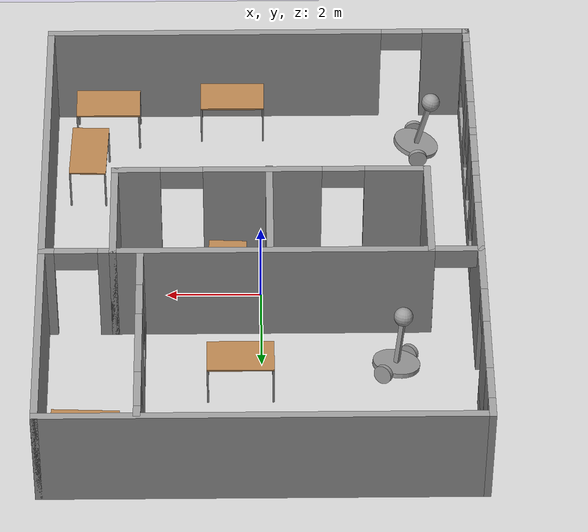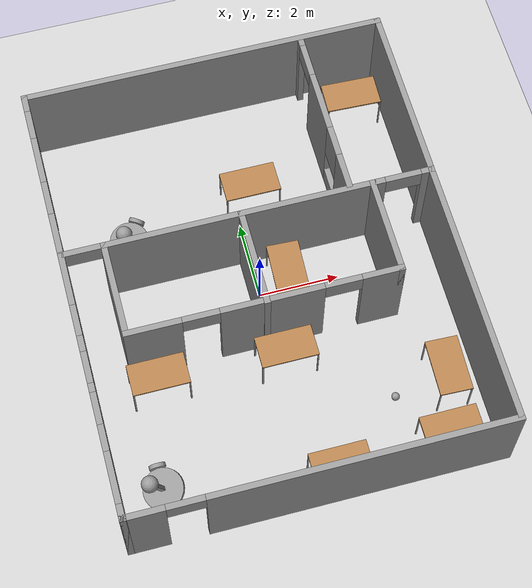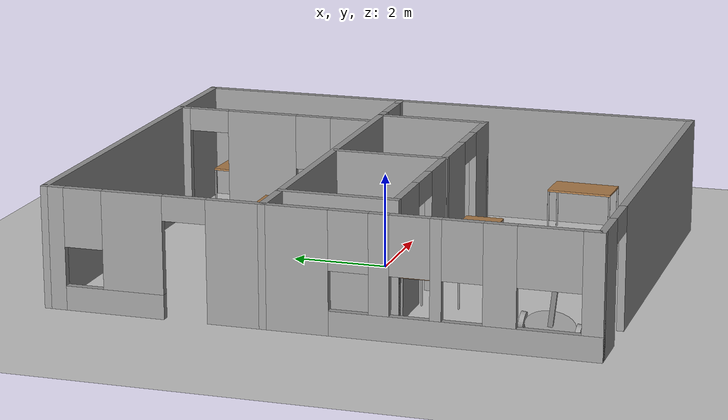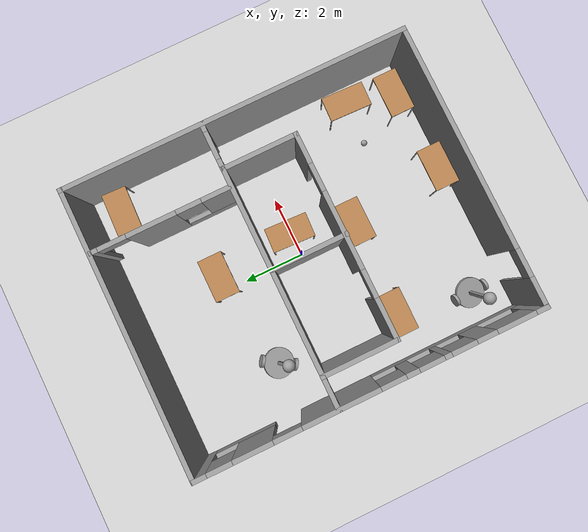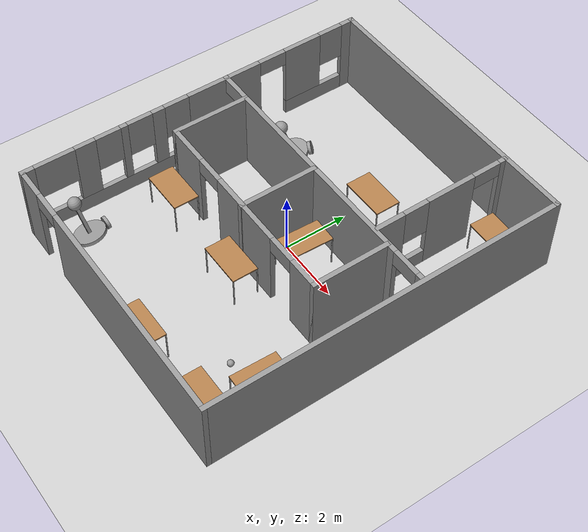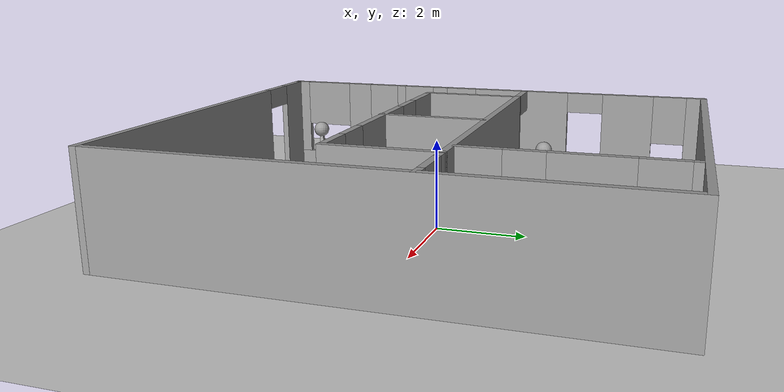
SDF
<sdf version="1.6">
 <world name="default">
  <light name="sun" type="directional">
   <pose>0 0 10 0 -0 0</pose>
   <diffuse>0.8 0.8 0.8 1</diffuse>
   <specular>0.1 0.1 0.1 1</specular>
   <attenuation>
    <range>1000</range>
    <constant>0.9</constant>
    <linear>0.01</linear>
    <quadratic>0.001</quadratic>
   </attenuation>
   <direction>-0.5 0.5 -1</direction>
  </light>
  <model name="ground_plane">
   <static>1</static>
   <link name="link">
    <collision name="collision">
     <geometry><plane><normal>0 0 1</normal><size>100 100</size></plane></geometry>
     <surface><friction><ode><mu>100</mu><mu2>50</mu2></ode></friction></surface>
    </collision>
    <visual name="visual">
     <cast_shadows>0</cast_shadows>
     <geometry><plane><normal>0 0 1</normal><size>100 100</size></plane></geometry>
     <material>
      <script><uri>file://media/materials/scripts/gazebo.material</uri><name>Gazebo/Grey</name></script>
     </material>
    </visual>
   </link>
  </model>
  <gravity>0 0 -9.8</gravity>
  <magnetic_field>6e-06 2.3e-05 -4.2e-05</magnetic_field>
  <atmosphere type="adiabatic"/>
  <physics name="default_physics" default="0" type="ode">
   <max_step_size>0.001</max_step_size>
   <real_time_factor>1</real_time_factor>
   <real_time_update_rate>1000</real_time_update_rate>
  </physics>
  <scene><ambient>0.4 0.4 0.4 1</ambient><background>0.7 0.7 0.7 1</background><shadows>1</shadows></scene>
  <spherical_coordinates>
   <surface_model>EARTH_WGS84</surface_model>
   <latitude_deg>0</latitude_deg>
   <longitude_deg>0</longitude_deg>
   <elevation>0</elevation>
   <heading_deg>0</heading_deg>
  </spherical_coordinates>
  <model name="bankinghall">
   <link name="Wall_10">
    <collision name="Wall_10_Collision">
     <geometry><box><size>0.16 0.15 2.5</size></box></geometry>
     <pose>0 0 1.25 0 -0 0</pose>
    </collision>
    <visual name="Wall_10_Visual">
     <pose>0 0 1.25 0 -0 0</pose>
     <geometry><box><size>0.16 0.15 2.5</size></box></geometry>
     <material>
      <script><uri>file://media/materials/scripts/gazebo.material</uri><name>Gazebo/Grey</name></script>
      <ambient>1 1 1 1</ambient>
     </material>
    </visual>
    <pose>-4.545 -5.55 0 0 -0 0</pose>
   </link>
   <link name="Wall_11">
    <collision name="Wall_11_Collision">
     <geometry><box><size>0.16 0.15 2.5</size></box></geometry>
     <pose>0 0 1.25 0 -0 0</pose>
    </collision>
    <visual name="Wall_11_Visual">
     <pose>0 0 1.25 0 -0 0</pose>
     <geometry><box><size>0.16 0.15 2.5</size></box></geometry>
     <material>
      <script><uri>file://media/materials/scripts/gazebo.material</uri><name>Gazebo/Grey</name></script>
      <ambient>1 1 1 1</ambient>
     </material>
    </visual>
    <pose>-4.545 -5.55 0 0 -0 3.14159</pose>
   </link>
   <link name="Wall_13">
    <pose>0 1.04456 0 0 -0 0</pose>
    <visual name="Wall_13_Visual_0">
     <pose>-4.56108 0 1.25 0 -0 0</pose>
     <geometry><box><size>0.127839 0.15 2.5</size></box></geometry>
     <material>
      <script><uri>file://media/materials/scripts/gazebo.material</uri><name>Gazebo/Grey</name></script>
      <ambient>1 1 1 1</ambient>
     </material>
    </visual>
    <collision name="Wall_13_Collision_0">
     <geometry><box><size>0.127839 0.15 2.5</size></box></geometry>
     <pose>-4.56108 0 1.25 0 -0 0</pose>
    </collision>
    <visual name="Wall_13_Visual_1">
     <pose>-0.104901 0 1.25 0 -0 0</pose>
     <geometry><box><size>6.98452 0.15 2.5</size></box></geometry>
     <material>
      <script><uri>file://media/materials/scripts/gazebo.material</uri><name>Gazebo/Grey</name></script>
      <ambient>1 1 1 1</ambient>
     </material>
    </visual>
    <collision name="Wall_13_Collision_1">
     <geometry><box><size>6.98452 0.15 2.5</size></box></geometry>
     <pose>-0.104901 0 1.25 0 -0 0</pose>
    </collision>
    <visual name="Wall_13_Visual_2">
     <pose>4.45618 0 1.25 0 -0 0</pose>
     <geometry><box><size>0.33764 0.15 2.5</size></box></geometry>
     <material>
      <script><uri>file://media/materials/scripts/gazebo.material</uri><name>Gazebo/Grey</name></script>
      <ambient>1 1 1 1</ambient>
     </material>
    </visual>
    <collision name="Wall_13_Collision_2">
     <geometry><box><size>0.33764 0.15 2.5</size></box></geometry>
     <pose>4.45618 0 1.25 0 -0 0</pose>
    </collision>
    <visual name="Wall_13_Visual_3">
     <pose>-4.04716 0 2.25 0 -0 0</pose>
     <geometry><box><size>0.9 0.15 0.5</size></box></geometry>
     <material>
      <script><uri>file://media/materials/scripts/gazebo.material</uri><name>Gazebo/Grey</name></script>
      <ambient>1 1 1 1</ambient>
     </material>
    </visual>
    <collision name="Wall_13_Collision_3">
     <geometry><box><size>0.9 0.15 0.5</size></box></geometry>
     <pose>-4.04716 0 2.25 0 -0 0</pose>
    </collision>
    <visual name="Wall_13_Visual_4">
     <pose>3.83736 0 2.25 0 -0 0</pose>
     <geometry><box><size>0.9 0.15 0.5</size></box></geometry>
     <material>
      <script><uri>file://media/materials/scripts/gazebo.material</uri><name>Gazebo/Grey</name></script>
      <ambient>1 1 1 1</ambient>
     </material>
    </visual>
    <collision name="Wall_13_Collision_4">
     <geometry><box><size>0.9 0.15 0.5</size></box></geometry>
     <pose>3.83736 0 2.25 0 -0 0</pose>
    </collision>
   </link>
   <link name="Wall_16">
    <collision name="Wall_16_Collision">
     <geometry><box><size>2.5 0.15 2.5</size></box></geometry>
     <pose>0 0 1.25 0 -0 0</pose>
    </collision>
    <visual name="Wall_16_Visual">
     <pose>0 0 1.25 0 -0 0</pose>
     <geometry><box><size>2.5 0.15 2.5</size></box></geometry>
     <material>
      <script><uri>file://media/materials/scripts/gazebo.material</uri><name>Gazebo/Grey</name></script>
      <ambient>1 1 1 1</ambient>
     </material>
    </visual>
    <pose>-3.52421 -0.13044 0 0 0 -1.5708</pose>
   </link>
   <link name="Wall_17">
    <pose>-0.224208 -1.30544 0 0 -0 0</pose>
    <visual name="Wall_17_Visual_0">
     <pose>-2.6775 0 1.25 0 -0 0</pose>
     <geometry><box><size>1.39499 0.15 2.5</size></box></geometry>
     <material>
      <script><uri>file://media/materials/scripts/gazebo.material</uri><name>Gazebo/Grey</name></script>
      <ambient>1 1 1 1</ambient>
     </material>
    </visual>
    <collision name="Wall_17_Collision_0">
     <geometry><box><size>1.39499 0.15 2.5</size></box></geometry>
     <pose>-2.6775 0 1.25 0 -0 0</pose>
    </collision>
    <visual name="Wall_17_Visual_1">
     <pose>0.179648 0 1.25 0 -0 0</pose>
     <geometry><box><size>2.51931 0.15 2.5</size></box></geometry>
     <material>
      <script><uri>file://media/materials/scripts/gazebo.material</uri><name>Gazebo/Grey</name></script>
      <ambient>1 1 1 1</ambient>
     </material>
    </visual>
    <collision name="Wall_17_Collision_1">
     <geometry><box><size>2.51931 0.15 2.5</size></box></geometry>
     <pose>0.179648 0 1.25 0 -0 0</pose>
    </collision>
    <visual name="Wall_17_Visual_2">
     <pose>2.85715 0 1.25 0 -0 0</pose>
     <geometry><box><size>1.0357 0.15 2.5</size></box></geometry>
     <material>
      <script><uri>file://media/materials/scripts/gazebo.material</uri><name>Gazebo/Grey</name></script>
      <ambient>1 1 1 1</ambient>
     </material>
    </visual>
    <collision name="Wall_17_Collision_2">
     <geometry><box><size>1.0357 0.15 2.5</size></box></geometry>
     <pose>2.85715 0 1.25 0 -0 0</pose>
    </collision>
    <visual name="Wall_17_Visual_3">
     <pose>-1.53001 0 2.25 0 -0 0</pose>
     <geometry><box><size>0.9 0.15 0.5</size></box></geometry>
     <material>
      <script><uri>file://media/materials/scripts/gazebo.material</uri><name>Gazebo/Grey</name></script>
      <ambient>1 1 1 1</ambient>
     </material>
    </visual>
    <collision name="Wall_17_Collision_3">
     <geometry><box><size>0.9 0.15 0.5</size></box></geometry>
     <pose>-1.53001 0 2.25 0 -0 0</pose>
    </collision>
    <visual name="Wall_17_Visual_4">
     <pose>1.8893 0 2.25 0 -0 0</pose>
     <geometry><box><size>0.9 0.15 0.5</size></box></geometry>
     <material>
      <script><uri>file://media/materials/scripts/gazebo.material</uri><name>Gazebo/Grey</name></script>
      <ambient>1 1 1 1</ambient>
     </material>
    </visual>
    <collision name="Wall_17_Collision_4">
     <geometry><box><size>0.9 0.15 0.5</size></box></geometry>
     <pose>1.8893 0 2.25 0 -0 0</pose>
    </collision>
   </link>
   <link name="Wall_18">
    <collision name="Wall_18_Collision">
     <geometry><box><size>2.5 0.15 2.5</size></box></geometry>
     <pose>0 0 1.25 0 -0 0</pose>
    </collision>
    <visual name="Wall_18_Visual">
     <pose>0 0 1.25 0 -0 0</pose>
     <geometry><box><size>2.5 0.15 2.5</size></box></geometry>
     <material>
      <script><uri>file://media/materials/scripts/gazebo.material</uri><name>Gazebo/Grey</name></script>
      <ambient>1 1 1 1</ambient>
     </material>
    </visual>
    <pose>3.07579 -0.13044 0 0 -0 1.5708</pose>
   </link>
   <link name="Wall_19">
    <collision name="Wall_19_Collision">
     <geometry><box><size>0.15 0.15 2.5</size></box></geometry>
     <pose>0 0 1.25 0 -0 0</pose>
    </collision>
    <visual name="Wall_19_Visual">
     <pose>0 0 1.25 0 -0 0</pose>
     <geometry><box><size>0.15 0.15 2.5</size></box></geometry>
     <material>
      <script><uri>file://media/materials/scripts/gazebo.material</uri><name>Gazebo/Grey</name></script>
      <ambient>1 1 1 1</ambient>
     </material>
    </visual>
    <pose>3.07579 1.04456 0 0 -0 0</pose>
   </link>
   <link name="Wall_2">
    <pose>-4.55 0 0 0 0 -1.5708</pose>
    <visual name="Wall_2_Visual_0">
     <pose>-5.38523 0 1.25 0 -0 0</pose>
     <geometry><box><size>0.479543 0.15 2.5</size></box></geometry>
     <material>
      <script><uri>file://media/materials/scripts/gazebo.material</uri><name>Gazebo/Grey</name></script>
      <ambient>1 1 1 1</ambient>
     </material>
    </visual>
    <collision name="Wall_2_Collision_0">
     <geometry><box><size>0.479543 0.15 2.5</size></box></geometry>
     <pose>-5.38523 0 1.25 0 -0 0</pose>
    </collision>
    <visual name="Wall_2_Visual_1">
     <pose>-0.949163 0 1.25 0 -0 0</pose>
     <geometry><box><size>2.46874 0.15 2.5</size></box></geometry>
     <material>
      <script><uri>file://media/materials/scripts/gazebo.material</uri><name>Gazebo/Grey</name></script>
      <ambient>1 1 1 1</ambient>
     </material>
    </visual>
    <collision name="Wall_2_Collision_1">
     <geometry><box><size>2.46874 0.15 2.5</size></box></geometry>
     <pose>-0.949163 0 1.25 0 -0 0</pose>
    </collision>
    <visual name="Wall_2_Visual_2">
     <pose>-4.11449 0 0.25 0 -0 0</pose>
     <geometry><box><size>2.06193 0.15 0.5</size></box></geometry>
     <material>
      <script><uri>file://media/materials/scripts/gazebo.material</uri><name>Gazebo/Grey</name></script>
      <ambient>1 1 1 1</ambient>
     </material>
    </visual>
    <collision name="Wall_2_Collision_2">
     <geometry><box><size>2.06193 0.15 0.5</size></box></geometry>
     <pose>-4.11449 0 0.25 0 -0 0</pose>
    </collision>
    <visual name="Wall_2_Visual_3">
     <pose>2.9551 0 0.25 0 -0 0</pose>
     <geometry><box><size>5.33979 0.15 0.5</size></box></geometry>
     <material>
      <script><uri>file://media/materials/scripts/gazebo.material</uri><name>Gazebo/Grey</name></script>
      <ambient>1 1 1 1</ambient>
     </material>
    </visual>
    <collision name="Wall_2_Collision_3">
     <geometry><box><size>5.33979 0.15 0.5</size></box></geometry>
     <pose>2.9551 0 0.25 0 -0 0</pose>
    </collision>
    <visual name="Wall_2_Visual_4">
     <pose>-3.71449 0 1.5 0 -0 0</pose>
     <geometry><box><size>1.26192 0.15 2</size></box></geometry>
     <material>
      <script><uri>file://media/materials/scripts/gazebo.material</uri><name>Gazebo/Grey</name></script>
      <ambient>1 1 1 1</ambient>
     </material>
    </visual>
    <collision name="Wall_2_Collision_4">
     <geometry><box><size>1.26192 0.15 2</size></box></geometry>
     <pose>-3.71449 0 1.5 0 -0 0</pose>
    </collision>
    <visual name="Wall_2_Visual_5">
     <pose>-3.71449 0 1.5 0 -0 0</pose>
     <geometry><box><size>1.26192 0.15 2</size></box></geometry>
     <material>
      <script><uri>file://media/materials/scripts/gazebo.material</uri><name>Gazebo/Grey</name></script>
      <ambient>1 1 1 1</ambient>
     </material>
    </visual>
    <collision name="Wall_2_Collision_5">
     <geometry><box><size>1.26192 0.15 2</size></box></geometry>
     <pose>-3.71449 0 1.5 0 -0 0</pose>
    </collision>
    <visual name="Wall_2_Visual_6">
     <pose>1.28861 0 1.5 0 -0 0</pose>
     <geometry><box><size>0.406815 0.15 2</size></box></geometry>
     <material>
      <script><uri>file://media/materials/scripts/gazebo.material</uri><name>Gazebo/Grey</name></script>
      <ambient>1 1 1 1</ambient>
     </material>
    </visual>
    <collision name="Wall_2_Collision_6">
     <geometry><box><size>0.406815 0.15 2</size></box></geometry>
     <pose>1.28861 0 1.5 0 -0 0</pose>
    </collision>
    <visual name="Wall_2_Visual_7">
     <pose>2.40492 0 1.5 0 -0 0</pose>
     <geometry><box><size>0.225792 0.15 2</size></box></geometry>
     <material>
      <script><uri>file://media/materials/scripts/gazebo.material</uri><name>Gazebo/Grey</name></script>
      <ambient>1 1 1 1</ambient>
     </material>
    </visual>
    <collision name="Wall_2_Collision_7">
     <geometry><box><size>0.225792 0.15 2</size></box></geometry>
     <pose>2.40492 0 1.5 0 -0 0</pose>
    </collision>
    <visual name="Wall_2_Visual_8">
     <pose>3.6419 0 1.5 0 -0 0</pose>
     <geometry><box><size>0.648177 0.15 2</size></box></geometry>
     <material>
      <script><uri>file://media/materials/scripts/gazebo.material</uri><name>Gazebo/Grey</name></script>
      <ambient>1 1 1 1</ambient>
     </material>
    </visual>
    <collision name="Wall_2_Collision_8">
     <geometry><box><size>0.648177 0.15 2</size></box></geometry>
     <pose>3.6419 0 1.5 0 -0 0</pose>
    </collision>
    <visual name="Wall_2_Visual_9">
     <pose>5.41674 0 1.5 0 -0 0</pose>
     <geometry><box><size>0.41651 0.15 2</size></box></geometry>
     <material>
      <script><uri>file://media/materials/scripts/gazebo.material</uri><name>Gazebo/Grey</name></script>
      <ambient>1 1 1 1</ambient>
     </material>
    </visual>
    <collision name="Wall_2_Collision_9">
     <geometry><box><size>0.41651 0.15 2</size></box></geometry>
     <pose>5.41674 0 1.5 0 -0 0</pose>
    </collision>
    <visual name="Wall_2_Visual_10">
     <pose>-4.74546 0 1.9 0 -0 0</pose>
     <geometry><box><size>0.8 0.15 1.2</size></box></geometry>
     <material>
      <script><uri>file://media/materials/scripts/gazebo.material</uri><name>Gazebo/Grey</name></script>
      <ambient>1 1 1 1</ambient>
     </material>
    </visual>
    <collision name="Wall_2_Collision_10">
     <geometry><box><size>0.8 0.15 1.2</size></box></geometry>
     <pose>-4.74546 0 1.9 0 -0 0</pose>
    </collision>
    <visual name="Wall_2_Visual_11">
     <pose>0.685207 0 1.9 0 -0 0</pose>
     <geometry><box><size>0.8 0.15 1.2</size></box></geometry>
     <material>
      <script><uri>file://media/materials/scripts/gazebo.material</uri><name>Gazebo/Grey</name></script>
      <ambient>1 1 1 1</ambient>
     </material>
    </visual>
    <collision name="Wall_2_Collision_11">
     <geometry><box><size>0.8 0.15 1.2</size></box></geometry>
     <pose>0.685207 0 1.9 0 -0 0</pose>
    </collision>
    <visual name="Wall_2_Visual_12">
     <pose>1.89202 0 1.9 0 -0 0</pose>
     <geometry><box><size>0.8 0.15 1.2</size></box></geometry>
     <material>
      <script><uri>file://media/materials/scripts/gazebo.material</uri><name>Gazebo/Grey</name></script>
      <ambient>1 1 1 1</ambient>
     </material>
    </visual>
    <collision name="Wall_2_Collision_12">
     <geometry><box><size>0.8 0.15 1.2</size></box></geometry>
     <pose>1.89202 0 1.9 0 -0 0</pose>
    </collision>
    <visual name="Wall_2_Visual_13">
     <pose>2.91781 0 1.9 0 -0 0</pose>
     <geometry><box><size>0.8 0.15 1.2</size></box></geometry>
     <material>
      <script><uri>file://media/materials/scripts/gazebo.material</uri><name>Gazebo/Grey</name></script>
      <ambient>1 1 1 1</ambient>
     </material>
    </visual>
    <collision name="Wall_2_Collision_13">
     <geometry><box><size>0.8 0.15 1.2</size></box></geometry>
     <pose>2.91781 0 1.9 0 -0 0</pose>
    </collision>
    <visual name="Wall_2_Visual_14">
     <pose>4.58724 0 1.9 0 -0 0</pose>
     <geometry><box><size>1.2425 0.15 1.2</size></box></geometry>
     <material>
      <script><uri>file://media/materials/scripts/gazebo.material</uri><name>Gazebo/Grey</name></script>
      <ambient>1 1 1 1</ambient>
     </material>
    </visual>
    <collision name="Wall_2_Collision_14">
     <geometry><box><size>1.2425 0.15 1.2</size></box></geometry>
     <pose>4.58724 0 1.9 0 -0 0</pose>
    </collision>
    <visual name="Wall_2_Visual_15">
     <pose>-2.63353 0 2.25 0 -0 0</pose>
     <geometry><box><size>0.9 0.15 0.5</size></box></geometry>
     <material>
      <script><uri>file://media/materials/scripts/gazebo.material</uri><name>Gazebo/Grey</name></script>
      <ambient>1 1 1 1</ambient>
     </material>
    </visual>
    <collision name="Wall_2_Collision_15">
     <geometry><box><size>0.9 0.15 0.5</size></box></geometry>
     <pose>-2.63353 0 2.25 0 -0 0</pose>
    </collision>
    <visual name="Wall_2_Visual_16">
     <pose>-2.63353 0 2.25 0 -0 0</pose>
     <geometry><box><size>0.9 0.15 0.5</size></box></geometry>
     <material>
      <script><uri>file://media/materials/scripts/gazebo.material</uri><name>Gazebo/Grey</name></script>
      <ambient>1 1 1 1</ambient>
     </material>
    </visual>
    <collision name="Wall_2_Collision_16">
     <geometry><box><size>0.9 0.15 0.5</size></box></geometry>
     <pose>-2.63353 0 2.25 0 -0 0</pose>
    </collision>
   </link>
   <link name="Wall_21">
    <pose>2.50986 3.31466 0 0 0 -1.5708</pose>
    <visual name="Wall_21_Visual_0">
     <pose>-2.11568 0 1.25 0 -0 0</pose>
     <geometry><box><size>0.268634 0.15 2.5</size></box></geometry>
     <material>
      <script><uri>file://media/materials/scripts/gazebo.material</uri><name>Gazebo/Grey</name></script>
      <ambient>1 1 1 1</ambient>
     </material>
    </visual>
    <collision name="Wall_21_Collision_0">
     <geometry><box><size>0.268634 0.15 2.5</size></box></geometry>
     <pose>-2.11568 0 1.25 0 -0 0</pose>
    </collision>
    <visual name="Wall_21_Visual_1">
     <pose>-0.289495 0 1.25 0 -0 0</pose>
     <geometry><box><size>1.58374 0.15 2.5</size></box></geometry>
     <material>
      <script><uri>file://media/materials/scripts/gazebo.material</uri><name>Gazebo/Grey</name></script>
      <ambient>1 1 1 1</ambient>
     </material>
    </visual>
    <collision name="Wall_21_Collision_1">
     <geometry><box><size>1.58374 0.15 2.5</size></box></geometry>
     <pose>-0.289495 0 1.25 0 -0 0</pose>
    </collision>
    <visual name="Wall_21_Visual_2">
     <pose>1.37619 0 0.25 0 -0 0</pose>
     <geometry><box><size>1.74762 0.15 0.5</size></box></geometry>
     <material>
      <script><uri>file://media/materials/scripts/gazebo.material</uri><name>Gazebo/Grey</name></script>
      <ambient>1 1 1 1</ambient>
     </material>
    </visual>
    <collision name="Wall_21_Collision_2">
     <geometry><box><size>1.74762 0.15 0.5</size></box></geometry>
     <pose>1.37619 0 0.25 0 -0 0</pose>
    </collision>
    <visual name="Wall_21_Visual_3">
     <pose>1.77619 0 1.5 0 -0 0</pose>
     <geometry><box><size>0.947623 0.15 2</size></box></geometry>
     <material>
      <script><uri>file://media/materials/scripts/gazebo.material</uri><name>Gazebo/Grey</name></script>
      <ambient>1 1 1 1</ambient>
     </material>
    </visual>
    <collision name="Wall_21_Collision_3">
     <geometry><box><size>0.947623 0.15 2</size></box></geometry>
     <pose>1.77619 0 1.5 0 -0 0</pose>
    </collision>
    <visual name="Wall_21_Visual_4">
     <pose>0.902377 0 1.9 0 -0 0</pose>
     <geometry><box><size>0.8 0.15 1.2</size></box></geometry>
     <material>
      <script><uri>file://media/materials/scripts/gazebo.material</uri><name>Gazebo/Grey</name></script>
      <ambient>1 1 1 1</ambient>
     </material>
    </visual>
    <collision name="Wall_21_Collision_4">
     <geometry><box><size>0.8 0.15 1.2</size></box></geometry>
     <pose>0.902377 0 1.9 0 -0 0</pose>
    </collision>
    <visual name="Wall_21_Visual_5">
     <pose>-1.53137 0 2.25 0 -0 0</pose>
     <geometry><box><size>0.9 0.15 0.5</size></box></geometry>
     <material>
      <script><uri>file://media/materials/scripts/gazebo.material</uri><name>Gazebo/Grey</name></script>
      <ambient>1 1 1 1</ambient>
     </material>
    </visual>
    <collision name="Wall_21_Collision_5">
     <geometry><box><size>0.9 0.15 0.5</size></box></geometry>
     <pose>-1.53137 0 2.25 0 -0 0</pose>
    </collision>
   </link>
   <link name="Wall_23">
    <collision name="Wall_23_Collision">
     <geometry><box><size>2.5 0.15 2.5</size></box></geometry>
     <pose>0 0 1.25 0 -0 0</pose>
    </collision>
    <visual name="Wall_23_Visual">
     <pose>0 0 1.25 0 -0 0</pose>
     <geometry><box><size>2.5 0.15 2.5</size></box></geometry>
     <material>
      <script><uri>file://media/materials/scripts/gazebo.material</uri><name>Gazebo/Grey</name></script>
      <ambient>1 1 1 1</ambient>
     </material>
    </visual>
    <pose>-0.185355 -0.150554 0 0 0 -1.5708</pose>
   </link>
   <link name="Wall_6">
    <collision name="Wall_6_Collision">
     <geometry><box><size>9.25 0.15 2.5</size></box></geometry>
     <pose>0 0 1.25 0 -0 0</pose>
    </collision>
    <visual name="Wall_6_Visual">
     <pose>0 0 1.25 0 -0 0</pose>
     <geometry><box><size>9.25 0.15 2.5</size></box></geometry>
     <material>
      <script><uri>file://media/materials/scripts/gazebo.material</uri><name>Gazebo/Grey</name></script>
      <ambient>1 1 1 1</ambient>
     </material>
    </visual>
    <pose>0 5.55 0 0 -0 0</pose>
   </link>
   <link name="Wall_7">
    <collision name="Wall_7_Collision">
     <geometry><box><size>11.25 0.15 2.5</size></box></geometry>
     <pose>0 0 1.25 0 -0 0</pose>
    </collision>
    <visual name="Wall_7_Visual">
     <pose>0 0 1.25 0 -0 0</pose>
     <geometry><box><size>11.25 0.15 2.5</size></box></geometry>
     <material>
      <script><uri>file://media/materials/scripts/gazebo.material</uri><name>Gazebo/Grey</name></script>
      <ambient>1 1 1 1</ambient>
     </material>
    </visual>
    <pose>4.55 0 0 0 0 -1.5708</pose>
   </link>
   <link name="Wall_8">
    <pose>0 -5.55 0 0 -0 3.14159</pose>
    <visual name="Wall_8_Visual_0">
     <pose>-0.966475 0 1.25 0 -0 0</pose>
     <geometry><box><size>7.31705 0.15 2.5</size></box></geometry>
     <material>
      <script><uri>file://media/materials/scripts/gazebo.material</uri><name>Gazebo/Grey</name></script>
      <ambient>1 1 1 1</ambient>
     </material>
    </visual>
    <collision name="Wall_8_Collision_0">
     <geometry><box><size>7.31705 0.15 2.5</size></box></geometry>
     <pose>-0.966475 0 1.25 0 -0 0</pose>
    </collision>
    <visual name="Wall_8_Visual_1">
     <pose>4.10853 0 1.25 0 -0 0</pose>
     <geometry><box><size>1.03295 0.15 2.5</size></box></geometry>
     <material>
      <script><uri>file://media/materials/scripts/gazebo.material</uri><name>Gazebo/Grey</name></script>
      <ambient>1 1 1 1</ambient>
     </material>
    </visual>
    <collision name="Wall_8_Collision_1">
     <geometry><box><size>1.03295 0.15 2.5</size></box></geometry>
     <pose>4.10853 0 1.25 0 -0 0</pose>
    </collision>
    <visual name="Wall_8_Visual_2">
     <pose>3.14205 0 2.25 0 -0 0</pose>
     <geometry><box><size>0.9 0.15 0.5</size></box></geometry>
     <material>
      <script><uri>file://media/materials/scripts/gazebo.material</uri><name>Gazebo/Grey</name></script>
      <ambient>1 1 1 1</ambient>
     </material>
    </visual>
    <collision name="Wall_8_Collision_2">
     <geometry><box><size>0.9 0.15 0.5</size></box></geometry>
     <pose>3.14205 0 2.25 0 -0 0</pose>
    </collision>
   </link>
   <link name="Wall_9">
    <collision name="Wall_9_Collision">
     <geometry><box><size>0.15 0.15 2.5</size></box></geometry>
     <pose>0 0 1.25 0 -0 0</pose>
    </collision>
    <visual name="Wall_9_Visual">
     <pose>0 0 1.25 0 -0 0</pose>
     <geometry><box><size>0.15 0.15 2.5</size></box></geometry>
     <material>
      <script><uri>file://media/materials/scripts/gazebo.material</uri><name>Gazebo/Grey</name></script>
      <ambient>1 1 1 1</ambient>
     </material>
    </visual>
    <pose>-4.55 -5.55 0 0 -0 0</pose>
   </link>
   <static>1</static>
  </model>
  <model name="table">
   <static>0</static>
   <link name="link">
    <collision name="surface">
     <pose>0 0 1 0 -0 0</pose>
     <geometry><box><size>1.5 0.8 0.03</size></box></geometry>
     <surface><friction><ode><mu>0.6</mu><mu2>0.6</mu2></ode></friction></surface>
    </collision>
    <visual name="visual1">
     <pose>0 0 1 0 -0 0</pose>
     <geometry><box><size>1.4 0.8 0.04</size></box></geometry>
     <material>
      <script><uri>file://media/materials/scripts/gazebo.material</uri><name>Gazebo/Wood</name></script>
     </material>
    </visual>
    <collision name="front_left_leg">
     <pose>0.68 0.38 0.5 0 -0 0</pose>
     <geometry><cylinder><radius>0.02</radius><length>1</length></cylinder></geometry>
    </collision>
    <visual name="front_left_leg">
     <pose>0.68 0.38 0.5 0 -0 0</pose>
     <geometry><cylinder><radius>0.02</radius><length>1</length></cylinder></geometry>
     <material>
      <script><uri>file://media/materials/scripts/gazebo.material</uri><name>Gazebo/Grey</name></script>
     </material>
    </visual>
    <collision name="front_right_leg">
     <pose>0.68 -0.38 0.5 0 -0 0</pose>
     <geometry><cylinder><radius>0.02</radius><length>1</length></cylinder></geometry>
    </collision>
    <visual name="front_right_leg">
     <pose>0.68 -0.38 0.5 0 -0 0</pose>
     <geometry><cylinder><radius>0.02</radius><length>1</length></cylinder></geometry>
     <material>
      <script><uri>file://media/materials/scripts/gazebo.material</uri><name>Gazebo/Grey</name></script>
     </material>
    </visual>
    <collision name="back_right_leg">
     <pose>-0.68 -0.38 0.5 0 -0 0</pose>
     <geometry><cylinder><radius>0.02</radius><length>1</length></cylinder></geometry>
    </collision>
    <visual name="back_right_leg">
     <pose>-0.68 -0.38 0.5 0 -0 0</pose>
     <geometry><cylinder><radius>0.02</radius><length>1</length></cylinder></geometry>
     <material>
      <script><uri>file://media/materials/scripts/gazebo.material</uri><name>Gazebo/Grey</name></script>
     </material>
    </visual>
    <collision name="back_left_leg">
     <pose>-0.68 0.38 0.5 0 -0 0</pose>
     <geometry><cylinder><radius>0.02</radius><length>1</length></cylinder></geometry>
    </collision>
    <visual name="back_left_leg">
     <pose>-0.68 0.38 0.5 0 -0 0</pose>
     <geometry><cylinder><radius>0.02</radius><length>1</length></cylinder></geometry>
     <material>
      <script><uri>file://media/materials/scripts/gazebo.material</uri><name>Gazebo/Grey</name></script>
     </material>
    </visual>
    <inertial>
     <inertia><ixx>1</ixx><ixy>0</ixy><ixz>0</ixz><iyy>1</iyy><iyz>0</iyz><izz>1</izz></inertia>
     <mass>1</mass>
    </inertial>
   </link>
   <pose>0.726138 0.064174 -9e-06 0 -1e-06 -1.61711</pose>
  </model>
  <model name="table_1">
   <static>0</static>
   <link name="link">
    <collision name="surface">
     <pose>0 0 1 0 -0 0</pose>
     <geometry><box><size>1.5 0.8 0.03</size></box></geometry>
     <surface><friction><ode><mu>0.6</mu><mu2>0.6</mu2></ode></friction></surface>
    </collision>
    <visual name="visual1">
     <pose>0 0 1 0 -0 0</pose>
     <geometry><box><size>1.4 0.8 0.04</size></box></geometry>
     <material>
      <script><uri>file://media/materials/scripts/gazebo.material</uri><name>Gazebo/Wood</name></script>
     </material>
    </visual>
    <collision name="front_left_leg">
     <pose>0.68 0.38 0.5 0 -0 0</pose>
     <geometry><cylinder><radius>0.02</radius><length>1</length></cylinder></geometry>
    </collision>
    <visual name="front_left_leg">
     <pose>0.68 0.38 0.5 0 -0 0</pose>
     <geometry><cylinder><radius>0.02</radius><length>1</length></cylinder></geometry>
     <material>
      <script><uri>file://media/materials/scripts/gazebo.material</uri><name>Gazebo/Grey</name></script>
     </material>
    </visual>
    <collision name="front_right_leg">
     <pose>0.68 -0.38 0.5 0 -0 0</pose>
     <geometry><cylinder><radius>0.02</radius><length>1</length></cylinder></geometry>
    </collision>
    <visual name="front_right_leg">
     <pose>0.68 -0.38 0.5 0 -0 0</pose>
     <geometry><cylinder><radius>0.02</radius><length>1</length></cylinder></geometry>
     <material>
      <script><uri>file://media/materials/scripts/gazebo.material</uri><name>Gazebo/Grey</name></script>
     </material>
    </visual>
    <collision name="back_right_leg">
     <pose>-0.68 -0.38 0.5 0 -0 0</pose>
     <geometry><cylinder><radius>0.02</radius><length>1</length></cylinder></geometry>
    </collision>
    <visual name="back_right_leg">
     <pose>-0.68 -0.38 0.5 0 -0 0</pose>
     <geometry><cylinder><radius>0.02</radius><length>1</length></cylinder></geometry>
     <material>
      <script><uri>file://media/materials/scripts/gazebo.material</uri><name>Gazebo/Grey</name></script>
     </material>
    </visual>
    <collision name="back_left_leg">
     <pose>-0.68 0.38 0.5 0 -0 0</pose>
     <geometry><cylinder><radius>0.02</radius><length>1</length></cylinder></geometry>
    </collision>
    <visual name="back_left_leg">
     <pose>-0.68 0.38 0.5 0 -0 0</pose>
     <geometry><cylinder><radius>0.02</radius><length>1</length></cylinder></geometry>
     <material>
      <script><uri>file://media/materials/scripts/gazebo.material</uri><name>Gazebo/Grey</name></script>
     </material>
    </visual>
    <inertial>
     <inertia><ixx>1</ixx><ixy>0</ixy><ixz>0</ixz><iyy>1</iyy><iyz>0</iyz><izz>1</izz></inertia>
     <mass>1</mass>
    </inertial>
   </link>
   <pose>0.444094 2.65705 -9e-06 0 -1e-06 0</pose>
  </model>
  <model name="robot">
   <link name="link_10">
    <pose>0 0 0.83 0 -0 0</pose>
    <inertial>
     <mass>1</mass>
     <inertia><ixx>0.1</ixx><ixy>0</ixy><ixz>0</ixz><iyy>0.1</iyy><iyz>0</iyz><izz>0.1</izz></inertia>
    </inertial>
    <visual name="visual">
     <geometry><sphere><radius>0.2</radius></sphere></geometry>
     <material>
      <lighting>1</lighting>
      <script><uri>file://media/materials/scripts/gazebo.material</uri><name>Gazebo/Grey</name></script>
      <ambient>0.3 0.3 0.3 1</ambient>
      <diffuse>0.7 0.7 0.7 1</diffuse>
      <specular>0.01 0.01 0.01 1</specular>
      <emissive>0 0 0 1</emissive>
      <shader type="vertex"><normal_map>__default__</normal_map></shader>
     </material>
    </visual>
    <collision name="collision">
     <geometry><sphere><radius>0.2</radius></sphere></geometry>
     <surface>
      <friction>
       <ode><mu>1</mu><mu2>1</mu2><fdir1>0 0 0</fdir1><slip1>0</slip1><slip2>0</slip2></ode>
       <torsional>
        <coefficient>1</coefficient>
        <patch_radius>0</patch_radius>
        <surface_radius>0</surface_radius>
        <use_patch_radius>1</use_patch_radius>
        <ode><slip>0</slip></ode>
       </torsional>
      </friction>
      <bounce><restitution_coefficient>0</restitution_coefficient><threshold>1e+06</threshold></bounce>
      <contact>
       <collide_without_contact>0</collide_without_contact>
       <collide_without_contact_bitmask>1</collide_without_contact_bitmask>
       <collide_bitmask>1</collide_bitmask>
       <ode>
        <soft_cfm>0</soft_cfm>
        <soft_erp>0.2</soft_erp>
        <kp>1e+13</kp>
        <kd>1</kd>
        <max_vel>0.01</max_vel>
        <min_depth>0</min_depth>
       </ode>
       <bullet>
        <split_impulse>1</split_impulse>
        <split_impulse_penetration_threshold>-0.01</split_impulse_penetration_threshold>
        <soft_cfm>0</soft_cfm>
        <soft_erp>0.2</soft_erp>
        <kp>1e+13</kp>
        <kd>1</kd>
       </bullet>
      </contact>
     </surface>
    </collision>
   </link>
   <link name="link_6">
    <pose>0 0 -0.32 0 -0 0</pose>
    <inertial>
     <mass>1</mass>
     <inertia><ixx>0.145833</ixx><ixy>0</ixy><ixz>0</ixz><iyy>0.145833</iyy><iyz>0</iyz><izz>0.125</izz></inertia>
    </inertial>
    <visual name="visual">
     <geometry><cylinder><radius>0.5</radius><length>0.1</length></cylinder></geometry>
     <material>
      <lighting>1</lighting>
      <script><uri>file://media/materials/scripts/gazebo.material</uri><name>Gazebo/Grey</name></script>
      <ambient>0.3 0.3 0.3 1</ambient>
      <diffuse>0.7 0.7 0.7 1</diffuse>
      <specular>0.01 0.01 0.01 1</specular>
      <emissive>0 0 0 1</emissive>
      <shader type="vertex"><normal_map>__default__</normal_map></shader>
     </material>
    </visual>
    <collision name="collision">
     <geometry><cylinder><radius>0.5</radius><length>0.1</length></cylinder></geometry>
     <surface>
      <friction>
       <ode><mu>1</mu><mu2>1</mu2><fdir1>0 0 0</fdir1><slip1>0</slip1><slip2>0</slip2></ode>
       <torsional>
        <coefficient>1</coefficient>
        <patch_radius>0</patch_radius>
        <surface_radius>0</surface_radius>
        <use_patch_radius>1</use_patch_radius>
        <ode><slip>0</slip></ode>
       </torsional>
      </friction>
      <bounce><restitution_coefficient>0</restitution_coefficient><threshold>1e+06</threshold></bounce>
      <contact>
       <collide_without_contact>0</collide_without_contact>
       <collide_without_contact_bitmask>1</collide_without_contact_bitmask>
       <collide_bitmask>1</collide_bitmask>
       <ode>
        <soft_cfm>0</soft_cfm>
        <soft_erp>0.2</soft_erp>
        <kp>1e+13</kp>
        <kd>1</kd>
        <max_vel>0.01</max_vel>
        <min_depth>0</min_depth>
       </ode>
       <bullet>
        <split_impulse>1</split_impulse>
        <split_impulse_penetration_threshold>-0.01</split_impulse_penetration_threshold>
        <soft_cfm>0</soft_cfm>
        <soft_erp>0.2</soft_erp>
        <kp>1e+13</kp>
        <kd>1</kd>
       </bullet>
      </contact>
     </surface>
    </collision>
   </link>
   <link name="link_7">
    <pose>0 0 0.13 0 -0 0</pose>
    <inertial>
     <mass>1</mass>
     <inertia>
      <ixx>0.166667</ixx>
      <ixy>0</ixy>
      <ixz>0</ixz>
      <iyy>0.166667</iyy>
      <iyz>0</iyz>
      <izz>0.166667</izz>
     </inertia>
    </inertial>
    <visual name="visual">
     <geometry><box><size>0.1 0.1 1</size></box></geometry>
     <material>
      <lighting>1</lighting>
      <script><uri>file://media/materials/scripts/gazebo.material</uri><name>Gazebo/Grey</name></script>
      <ambient>0.3 0.3 0.3 1</ambient>
      <diffuse>0.7 0.7 0.7 1</diffuse>
      <specular>0.01 0.01 0.01 1</specular>
      <emissive>0 0 0 1</emissive>
      <shader type="vertex"><normal_map>__default__</normal_map></shader>
     </material>
    </visual>
    <collision name="collision">
     <geometry><box><size>0.1 0.1 1</size></box></geometry>
     <surface>
      <friction>
       <ode><mu>1</mu><mu2>1</mu2><fdir1>0 0 0</fdir1><slip1>0</slip1><slip2>0</slip2></ode>
       <torsional>
        <coefficient>1</coefficient>
        <patch_radius>0</patch_radius>
        <surface_radius>0</surface_radius>
        <use_patch_radius>1</use_patch_radius>
        <ode><slip>0</slip></ode>
       </torsional>
      </friction>
      <bounce><restitution_coefficient>0</restitution_coefficient><threshold>1e+06</threshold></bounce>
      <contact>
       <collide_without_contact>0</collide_without_contact>
       <collide_without_contact_bitmask>1</collide_without_contact_bitmask>
       <collide_bitmask>1</collide_bitmask>
       <ode>
        <soft_cfm>0</soft_cfm>
        <soft_erp>0.2</soft_erp>
        <kp>1e+13</kp>
        <kd>1</kd>
        <max_vel>0.01</max_vel>
        <min_depth>0</min_depth>
       </ode>
       <bullet>
        <split_impulse>1</split_impulse>
        <split_impulse_penetration_threshold>-0.01</split_impulse_penetration_threshold>
        <soft_cfm>0</soft_cfm>
        <soft_erp>0.2</soft_erp>
        <kp>1e+13</kp>
        <kd>1</kd>
       </bullet>
      </contact>
     </surface>
    </collision>
   </link>
   <link name="link_8">
    <pose>0 -0.550241 -0.32 1.572 -0 0</pose>
    <inertial>
     <mass>1</mass>
     <inertia><ixx>0.145833</ixx><ixy>0</ixy><ixz>0</ixz><iyy>0.145833</iyy><iyz>0</iyz><izz>0.125</izz></inertia>
    </inertial>
    <visual name="visual">
     <geometry><cylinder><radius>0.2</radius><length>0.1</length></cylinder></geometry>
     <material>
      <lighting>1</lighting>
      <script><uri>file://media/materials/scripts/gazebo.material</uri><name>Gazebo/Grey</name></script>
      <ambient>0.3 0.3 0.3 1</ambient>
      <diffuse>0.7 0.7 0.7 1</diffuse>
      <specular>0.01 0.01 0.01 1</specular>
      <emissive>0 0 0 1</emissive>
      <shader type="vertex"><normal_map>__default__</normal_map></shader>
     </material>
    </visual>
    <collision name="collision">
     <geometry><cylinder><radius>0.2</radius><length>0.1</length></cylinder></geometry>
     <surface>
      <friction>
       <ode><mu>1</mu><mu2>1</mu2><fdir1>0 0 0</fdir1><slip1>0</slip1><slip2>0</slip2></ode>
       <torsional>
        <coefficient>1</coefficient>
        <patch_radius>0</patch_radius>
        <surface_radius>0</surface_radius>
        <use_patch_radius>1</use_patch_radius>
        <ode><slip>0</slip></ode>
       </torsional>
      </friction>
      <bounce><restitution_coefficient>0</restitution_coefficient><threshold>1e+06</threshold></bounce>
      <contact>
       <collide_without_contact>0</collide_without_contact>
       <collide_without_contact_bitmask>1</collide_without_contact_bitmask>
       <collide_bitmask>1</collide_bitmask>
       <ode>
        <soft_cfm>0</soft_cfm>
        <soft_erp>0.2</soft_erp>
        <kp>1e+13</kp>
        <kd>1</kd>
        <max_vel>0.01</max_vel>
        <min_depth>0</min_depth>
       </ode>
       <bullet>
        <split_impulse>1</split_impulse>
        <split_impulse_penetration_threshold>-0.01</split_impulse_penetration_threshold>
        <soft_cfm>0</soft_cfm>
        <soft_erp>0.2</soft_erp>
        <kp>1e+13</kp>
        <kd>1</kd>
       </bullet>
      </contact>
     </surface>
    </collision>
   </link>
   <link name="link_8_clone">
    <pose>0 0.550241 -0.32 1.572 -0 0</pose>
    <inertial>
     <mass>1</mass>
     <inertia><ixx>0.145833</ixx><ixy>0</ixy><ixz>0</ixz><iyy>0.145833</iyy><iyz>0</iyz><izz>0.125</izz></inertia>
    </inertial>
    <visual name="visual">
     <geometry><cylinder><radius>0.2</radius><length>0.1</length></cylinder></geometry>
     <material>
      <lighting>1</lighting>
      <script><uri>file://media/materials/scripts/gazebo.material</uri><name>Gazebo/Grey</name></script>
      <ambient>0.3 0.3 0.3 1</ambient>
      <diffuse>0.7 0.7 0.7 1</diffuse>
      <specular>0.01 0.01 0.01 1</specular>
      <emissive>0 0 0 1</emissive>
      <shader type="vertex"><normal_map>__default__</normal_map></shader>
     </material>
    </visual>
    <collision name="collision">
     <geometry><cylinder><radius>0.2</radius><length>0.1</length></cylinder></geometry>
     <surface>
      <friction>
       <ode><mu>1</mu><mu2>1</mu2><fdir1>0 0 0</fdir1><slip1>0</slip1><slip2>0</slip2></ode>
       <torsional>
        <coefficient>1</coefficient>
        <patch_radius>0</patch_radius>
        <surface_radius>0</surface_radius>
        <use_patch_radius>1</use_patch_radius>
        <ode><slip>0</slip></ode>
       </torsional>
      </friction>
      <bounce><restitution_coefficient>0</restitution_coefficient><threshold>1e+06</threshold></bounce>
      <contact>
       <collide_without_contact>0</collide_without_contact>
       <collide_without_contact_bitmask>1</collide_without_contact_bitmask>
       <collide_bitmask>1</collide_bitmask>
       <ode>
        <soft_cfm>0</soft_cfm>
        <soft_erp>0.2</soft_erp>
        <kp>1e+13</kp>
        <kd>1</kd>
        <max_vel>0.01</max_vel>
        <min_depth>0</min_depth>
       </ode>
       <bullet>
        <split_impulse>1</split_impulse>
        <split_impulse_penetration_threshold>-0.01</split_impulse_penetration_threshold>
        <soft_cfm>0</soft_cfm>
        <soft_erp>0.2</soft_erp>
        <kp>1e+13</kp>
        <kd>1</kd>
       </bullet>
      </contact>
     </surface>
    </collision>
   </link>
   <joint name="link_6_JOINT_10" type="revolute">
    <parent>link_6</parent>
    <child>link_7</child>
    <axis>
     <xyz>1 0 0</xyz>
     <use_parent_model_frame>0</use_parent_model_frame>
     <limit>
      <lower>-1.79769e+308</lower>
      <upper>1.79769e+308</upper>
      <effort>-1</effort>
      <velocity>-1</velocity>
     </limit>
     <dynamics>
      <spring_reference>0</spring_reference>
      <spring_stiffness>0</spring_stiffness>
      <damping>0</damping>
     </dynamics>
    </axis>
    <physics>
     <ode><limit><cfm>0</cfm><erp>0.2</erp></limit><suspension><cfm>0</cfm><erp>0.2</erp></suspension></ode>
    </physics>
   </joint>
   <joint name="link_6_JOINT_6" type="fixed">
    <parent>link_6</parent>
    <child>link_7</child>
    <physics>
     <ode><limit><cfm>0</cfm><erp>0.2</erp></limit><suspension><cfm>0</cfm><erp>0.2</erp></suspension></ode>
    </physics>
   </joint>
   <joint name="link_6_JOINT_7" type="revolute">
    <parent>link_6</parent>
    <child>link_8</child>
    <axis>
     <xyz>0 0 1</xyz>
     <use_parent_model_frame>0</use_parent_model_frame>
     <limit>
      <lower>-1.79769e+308</lower>
      <upper>1.79769e+308</upper>
      <effort>-1</effort>
      <velocity>-1</velocity>
     </limit>
     <dynamics>
      <spring_reference>0</spring_reference>
      <spring_stiffness>0</spring_stiffness>
      <damping>0</damping>
     </dynamics>
    </axis>
    <physics>
     <ode><limit><cfm>0</cfm><erp>0.2</erp></limit><suspension><cfm>0</cfm><erp>0.2</erp></suspension></ode>
    </physics>
   </joint>
   <joint name="link_6_JOINT_8" type="revolute">
    <parent>link_6</parent>
    <child>link_8_clone</child>
    <axis>
     <xyz>0 0 1</xyz>
     <use_parent_model_frame>0</use_parent_model_frame>
     <limit>
      <lower>-1.79769e+308</lower>
      <upper>1.79769e+308</upper>
      <effort>-1</effort>
      <velocity>-1</velocity>
     </limit>
     <dynamics>
      <spring_reference>0</spring_reference>
      <spring_stiffness>0</spring_stiffness>
      <damping>0</damping>
     </dynamics>
    </axis>
    <physics>
     <ode><limit><cfm>0</cfm><erp>0.2</erp></limit><suspension><cfm>0</cfm><erp>0.2</erp></suspension></ode>
    </physics>
   </joint>
   <joint name="link_7_JOINT_11" type="revolute">
    <parent>link_7</parent>
    <child>link_10</child>
    <axis>
     <xyz>0 0 1</xyz>
     <use_parent_model_frame>0</use_parent_model_frame>
     <limit>
      <lower>-1.79769e+308</lower>
      <upper>1.79769e+308</upper>
      <effort>-1</effort>
      <velocity>-1</velocity>
     </limit>
     <dynamics>
      <spring_reference>0</spring_reference>
      <spring_stiffness>0</spring_stiffness>
      <damping>0</damping>
     </dynamics>
    </axis>
    <physics>
     <ode><limit><cfm>0</cfm><erp>0.2</erp></limit><suspension><cfm>0</cfm><erp>0.2</erp></suspension></ode>
    </physics>
   </joint>
   <static>0</static>
   <pose>-2.8524 2.08645 0.504821 -0.304704 -0.056898 2.57876</pose>
  </model>
  <model name="robot_1">
   <link name="link_10">
    <pose>0 0 0.83 0 -0 0</pose>
    <inertial>
     <mass>1</mass>
     <inertia><ixx>0.1</ixx><ixy>0</ixy><ixz>0</ixz><iyy>0.1</iyy><iyz>0</iyz><izz>0.1</izz></inertia>
    </inertial>
    <visual name="visual">
     <geometry><sphere><radius>0.2</radius></sphere></geometry>
     <material>
      <lighting>1</lighting>
      <script><uri>file://media/materials/scripts/gazebo.material</uri><name>Gazebo/Grey</name></script>
      <ambient>0.3 0.3 0.3 1</ambient>
      <diffuse>0.7 0.7 0.7 1</diffuse>
      <specular>0.01 0.01 0.01 1</specular>
      <emissive>0 0 0 1</emissive>
      <shader type="vertex"><normal_map>__default__</normal_map></shader>
     </material>
    </visual>
    <collision name="collision">
     <geometry><sphere><radius>0.2</radius></sphere></geometry>
     <surface>
      <friction>
       <ode><mu>1</mu><mu2>1</mu2><fdir1>0 0 0</fdir1><slip1>0</slip1><slip2>0</slip2></ode>
       <torsional>
        <coefficient>1</coefficient>
        <patch_radius>0</patch_radius>
        <surface_radius>0</surface_radius>
        <use_patch_radius>1</use_patch_radius>
        <ode><slip>0</slip></ode>
       </torsional>
      </friction>
      <bounce><restitution_coefficient>0</restitution_coefficient><threshold>1e+06</threshold></bounce>
      <contact>
       <collide_without_contact>0</collide_without_contact>
       <collide_without_contact_bitmask>1</collide_without_contact_bitmask>
       <collide_bitmask>1</collide_bitmask>
       <ode>
        <soft_cfm>0</soft_cfm>
        <soft_erp>0.2</soft_erp>
        <kp>1e+13</kp>
        <kd>1</kd>
        <max_vel>0.01</max_vel>
        <min_depth>0</min_depth>
       </ode>
       <bullet>
        <split_impulse>1</split_impulse>
        <split_impulse_penetration_threshold>-0.01</split_impulse_penetration_threshold>
        <soft_cfm>0</soft_cfm>
        <soft_erp>0.2</soft_erp>
        <kp>1e+13</kp>
        <kd>1</kd>
       </bullet>
      </contact>
     </surface>
    </collision>
   </link>
   <link name="link_6">
    <pose>0 0 -0.32 0 -0 0</pose>
    <inertial>
     <mass>1</mass>
     <inertia><ixx>0.145833</ixx><ixy>0</ixy><ixz>0</ixz><iyy>0.145833</iyy><iyz>0</iyz><izz>0.125</izz></inertia>
    </inertial>
    <visual name="visual">
     <geometry><cylinder><radius>0.5</radius><length>0.1</length></cylinder></geometry>
     <material>
      <lighting>1</lighting>
      <script><uri>file://media/materials/scripts/gazebo.material</uri><name>Gazebo/Grey</name></script>
      <ambient>0.3 0.3 0.3 1</ambient>
      <diffuse>0.7 0.7 0.7 1</diffuse>
      <specular>0.01 0.01 0.01 1</specular>
      <emissive>0 0 0 1</emissive>
      <shader type="vertex"><normal_map>__default__</normal_map></shader>
     </material>
    </visual>
    <collision name="collision">
     <geometry><cylinder><radius>0.5</radius><length>0.1</length></cylinder></geometry>
     <surface>
      <friction>
       <ode><mu>1</mu><mu2>1</mu2><fdir1>0 0 0</fdir1><slip1>0</slip1><slip2>0</slip2></ode>
       <torsional>
        <coefficient>1</coefficient>
        <patch_radius>0</patch_radius>
        <surface_radius>0</surface_radius>
        <use_patch_radius>1</use_patch_radius>
        <ode><slip>0</slip></ode>
       </torsional>
      </friction>
      <bounce><restitution_coefficient>0</restitution_coefficient><threshold>1e+06</threshold></bounce>
      <contact>
       <collide_without_contact>0</collide_without_contact>
       <collide_without_contact_bitmask>1</collide_without_contact_bitmask>
       <collide_bitmask>1</collide_bitmask>
       <ode>
        <soft_cfm>0</soft_cfm>
        <soft_erp>0.2</soft_erp>
        <kp>1e+13</kp>
        <kd>1</kd>
        <max_vel>0.01</max_vel>
        <min_depth>0</min_depth>
       </ode>
       <bullet>
        <split_impulse>1</split_impulse>
        <split_impulse_penetration_threshold>-0.01</split_impulse_penetration_threshold>
        <soft_cfm>0</soft_cfm>
        <soft_erp>0.2</soft_erp>
        <kp>1e+13</kp>
        <kd>1</kd>
       </bullet>
      </contact>
     </surface>
    </collision>
   </link>
   <link name="link_7">
    <pose>0 0 0.13 0 -0 0</pose>
    <inertial>
     <mass>1</mass>
     <inertia>
      <ixx>0.166667</ixx>
      <ixy>0</ixy>
      <ixz>0</ixz>
      <iyy>0.166667</iyy>
      <iyz>0</iyz>
      <izz>0.166667</izz>
     </inertia>
    </inertial>
    <visual name="visual">
     <geometry><box><size>0.1 0.1 1</size></box></geometry>
     <material>
      <lighting>1</lighting>
      <script><uri>file://media/materials/scripts/gazebo.material</uri><name>Gazebo/Grey</name></script>
      <ambient>0.3 0.3 0.3 1</ambient>
      <diffuse>0.7 0.7 0.7 1</diffuse>
      <specular>0.01 0.01 0.01 1</specular>
      <emissive>0 0 0 1</emissive>
      <shader type="vertex"><normal_map>__default__</normal_map></shader>
     </material>
    </visual>
    <collision name="collision">
     <geometry><box><size>0.1 0.1 1</size></box></geometry>
     <surface>
      <friction>
       <ode><mu>1</mu><mu2>1</mu2><fdir1>0 0 0</fdir1><slip1>0</slip1><slip2>0</slip2></ode>
       <torsional>
        <coefficient>1</coefficient>
        <patch_radius>0</patch_radius>
        <surface_radius>0</surface_radius>
        <use_patch_radius>1</use_patch_radius>
        <ode><slip>0</slip></ode>
       </torsional>
      </friction>
      <bounce><restitution_coefficient>0</restitution_coefficient><threshold>1e+06</threshold></bounce>
      <contact>
       <collide_without_contact>0</collide_without_contact>
       <collide_without_contact_bitmask>1</collide_without_contact_bitmask>
       <collide_bitmask>1</collide_bitmask>
       <ode>
        <soft_cfm>0</soft_cfm>
        <soft_erp>0.2</soft_erp>
        <kp>1e+13</kp>
        <kd>1</kd>
        <max_vel>0.01</max_vel>
        <min_depth>0</min_depth>
       </ode>
       <bullet>
        <split_impulse>1</split_impulse>
        <split_impulse_penetration_threshold>-0.01</split_impulse_penetration_threshold>
        <soft_cfm>0</soft_cfm>
        <soft_erp>0.2</soft_erp>
        <kp>1e+13</kp>
        <kd>1</kd>
       </bullet>
      </contact>
     </surface>
    </collision>
   </link>
   <link name="link_8">
    <pose>0 -0.550241 -0.32 1.572 -0 0</pose>
    <inertial>
     <mass>1</mass>
     <inertia><ixx>0.145833</ixx><ixy>0</ixy><ixz>0</ixz><iyy>0.145833</iyy><iyz>0</iyz><izz>0.125</izz></inertia>
    </inertial>
    <visual name="visual">
     <geometry><cylinder><radius>0.2</radius><length>0.1</length></cylinder></geometry>
     <material>
      <lighting>1</lighting>
      <script><uri>file://media/materials/scripts/gazebo.material</uri><name>Gazebo/Grey</name></script>
      <ambient>0.3 0.3 0.3 1</ambient>
      <diffuse>0.7 0.7 0.7 1</diffuse>
      <specular>0.01 0.01 0.01 1</specular>
      <emissive>0 0 0 1</emissive>
      <shader type="vertex"><normal_map>__default__</normal_map></shader>
     </material>
    </visual>
    <collision name="collision">
     <geometry><cylinder><radius>0.2</radius><length>0.1</length></cylinder></geometry>
     <surface>
      <friction>
       <ode><mu>1</mu><mu2>1</mu2><fdir1>0 0 0</fdir1><slip1>0</slip1><slip2>0</slip2></ode>
       <torsional>
        <coefficient>1</coefficient>
        <patch_radius>0</patch_radius>
        <surface_radius>0</surface_radius>
        <use_patch_radius>1</use_patch_radius>
        <ode><slip>0</slip></ode>
       </torsional>
      </friction>
      <bounce><restitution_coefficient>0</restitution_coefficient><threshold>1e+06</threshold></bounce>
      <contact>
       <collide_without_contact>0</collide_without_contact>
       <collide_without_contact_bitmask>1</collide_without_contact_bitmask>
       <collide_bitmask>1</collide_bitmask>
       <ode>
        <soft_cfm>0</soft_cfm>
        <soft_erp>0.2</soft_erp>
        <kp>1e+13</kp>
        <kd>1</kd>
        <max_vel>0.01</max_vel>
        <min_depth>0</min_depth>
       </ode>
       <bullet>
        <split_impulse>1</split_impulse>
        <split_impulse_penetration_threshold>-0.01</split_impulse_penetration_threshold>
        <soft_cfm>0</soft_cfm>
        <soft_erp>0.2</soft_erp>
        <kp>1e+13</kp>
        <kd>1</kd>
       </bullet>
      </contact>
     </surface>
    </collision>
   </link>
   <link name="link_8_clone">
    <pose>0 0.550241 -0.32 1.572 -0 0</pose>
    <inertial>
     <mass>1</mass>
     <inertia><ixx>0.145833</ixx><ixy>0</ixy><ixz>0</ixz><iyy>0.145833</iyy><iyz>0</iyz><izz>0.125</izz></inertia>
    </inertial>
    <visual name="visual">
     <geometry><cylinder><radius>0.2</radius><length>0.1</length></cylinder></geometry>
     <material>
      <lighting>1</lighting>
      <script><uri>file://media/materials/scripts/gazebo.material</uri><name>Gazebo/Grey</name></script>
      <ambient>0.3 0.3 0.3 1</ambient>
      <diffuse>0.7 0.7 0.7 1</diffuse>
      <specular>0.01 0.01 0.01 1</specular>
      <emissive>0 0 0 1</emissive>
      <shader type="vertex"><normal_map>__default__</normal_map></shader>
     </material>
    </visual>
    <collision name="collision">
     <geometry><cylinder><radius>0.2</radius><length>0.1</length></cylinder></geometry>
     <surface>
      <friction>
       <ode><mu>1</mu><mu2>1</mu2><fdir1>0 0 0</fdir1><slip1>0</slip1><slip2>0</slip2></ode>
       <torsional>
        <coefficient>1</coefficient>
        <patch_radius>0</patch_radius>
        <surface_radius>0</surface_radius>
        <use_patch_radius>1</use_patch_radius>
        <ode><slip>0</slip></ode>
       </torsional>
      </friction>
      <bounce><restitution_coefficient>0</restitution_coefficient><threshold>1e+06</threshold></bounce>
      <contact>
       <collide_without_contact>0</collide_without_contact>
       <collide_without_contact_bitmask>1</collide_without_contact_bitmask>
       <collide_bitmask>1</collide_bitmask>
       <ode>
        <soft_cfm>0</soft_cfm>
        <soft_erp>0.2</soft_erp>
        <kp>1e+13</kp>
        <kd>1</kd>
        <max_vel>0.01</max_vel>
        <min_depth>0</min_depth>
       </ode>
       <bullet>
        <split_impulse>1</split_impulse>
        <split_impulse_penetration_threshold>-0.01</split_impulse_penetration_threshold>
        <soft_cfm>0</soft_cfm>
        <soft_erp>0.2</soft_erp>
        <kp>1e+13</kp>
        <kd>1</kd>
       </bullet>
      </contact>
     </surface>
    </collision>
   </link>
   <joint name="link_6_JOINT_10" type="revolute">
    <parent>link_6</parent>
    <child>link_7</child>
    <axis>
     <xyz>1 0 0</xyz>
     <use_parent_model_frame>0</use_parent_model_frame>
     <limit>
      <lower>-1.79769e+308</lower>
      <upper>1.79769e+308</upper>
      <effort>-1</effort>
      <velocity>-1</velocity>
     </limit>
     <dynamics>
      <spring_reference>0</spring_reference>
      <spring_stiffness>0</spring_stiffness>
      <damping>0</damping>
     </dynamics>
    </axis>
    <physics>
     <ode><limit><cfm>0</cfm><erp>0.2</erp></limit><suspension><cfm>0</cfm><erp>0.2</erp></suspension></ode>
    </physics>
   </joint>
   <joint name="link_6_JOINT_6" type="fixed">
    <parent>link_6</parent>
    <child>link_7</child>
    <physics>
     <ode><limit><cfm>0</cfm><erp>0.2</erp></limit><suspension><cfm>0</cfm><erp>0.2</erp></suspension></ode>
    </physics>
   </joint>
   <joint name="link_6_JOINT_7" type="revolute">
    <parent>link_6</parent>
    <child>link_8</child>
    <axis>
     <xyz>0 0 1</xyz>
     <use_parent_model_frame>0</use_parent_model_frame>
     <limit>
      <lower>-1.79769e+308</lower>
      <upper>1.79769e+308</upper>
      <effort>-1</effort>
      <velocity>-1</velocity>
     </limit>
     <dynamics>
      <spring_reference>0</spring_reference>
      <spring_stiffness>0</spring_stiffness>
      <damping>0</damping>
     </dynamics>
    </axis>
    <physics>
     <ode><limit><cfm>0</cfm><erp>0.2</erp></limit><suspension><cfm>0</cfm><erp>0.2</erp></suspension></ode>
    </physics>
   </joint>
   <joint name="link_6_JOINT_8" type="revolute">
    <parent>link_6</parent>
    <child>link_8_clone</child>
    <axis>
     <xyz>0 0 1</xyz>
     <use_parent_model_frame>0</use_parent_model_frame>
     <limit>
      <lower>-1.79769e+308</lower>
      <upper>1.79769e+308</upper>
      <effort>-1</effort>
      <velocity>-1</velocity>
     </limit>
     <dynamics>
      <spring_reference>0</spring_reference>
      <spring_stiffness>0</spring_stiffness>
      <damping>0</damping>
     </dynamics>
    </axis>
    <physics>
     <ode><limit><cfm>0</cfm><erp>0.2</erp></limit><suspension><cfm>0</cfm><erp>0.2</erp></suspension></ode>
    </physics>
   </joint>
   <joint name="link_7_JOINT_11" type="revolute">
    <parent>link_7</parent>
    <child>link_10</child>
    <axis>
     <xyz>0 0 1</xyz>
     <use_parent_model_frame>0</use_parent_model_frame>
     <limit>
      <lower>-1.79769e+308</lower>
      <upper>1.79769e+308</upper>
      <effort>-1</effort>
      <velocity>-1</velocity>
     </limit>
     <dynamics>
      <spring_reference>0</spring_reference>
      <spring_stiffness>0</spring_stiffness>
      <damping>0</damping>
     </dynamics>
    </axis>
    <physics>
     <ode><limit><cfm>0</cfm><erp>0.2</erp></limit><suspension><cfm>0</cfm><erp>0.2</erp></suspension></ode>
    </physics>
   </joint>
   <static>0</static>
   <pose>-3.56375 -4.40744 0.504823 0.158446 -0.267354 -0.006831</pose>
  </model>
  <model name="table_2">
   <static>0</static>
   <link name="link">
    <collision name="surface">
     <pose>0 0 1 0 -0 0</pose>
     <geometry><box><size>1.5 0.8 0.03</size></box></geometry>
     <surface><friction><ode><mu>0.6</mu><mu2>0.6</mu2></ode></friction></surface>
    </collision>
    <visual name="visual1">
     <pose>0 0 1 0 -0 0</pose>
     <geometry><box><size>1.4 0.8 0.04</size></box></geometry>
     <material>
      <script><uri>file://media/materials/scripts/gazebo.material</uri><name>Gazebo/Wood</name></script>
     </material>
    </visual>
    <collision name="front_left_leg">
     <pose>0.68 0.38 0.5 0 -0 0</pose>
     <geometry><cylinder><radius>0.02</radius><length>1</length></cylinder></geometry>
    </collision>
    <visual name="front_left_leg">
     <pose>0.68 0.38 0.5 0 -0 0</pose>
     <geometry><cylinder><radius>0.02</radius><length>1</length></cylinder></geometry>
     <material>
      <script><uri>file://media/materials/scripts/gazebo.material</uri><name>Gazebo/Grey</name></script>
     </material>
    </visual>
    <collision name="front_right_leg">
     <pose>0.68 -0.38 0.5 0 -0 0</pose>
     <geometry><cylinder><radius>0.02</radius><length>1</length></cylinder></geometry>
    </collision>
    <visual name="front_right_leg">
     <pose>0.68 -0.38 0.5 0 -0 0</pose>
     <geometry><cylinder><radius>0.02</radius><length>1</length></cylinder></geometry>
     <material>
      <script><uri>file://media/materials/scripts/gazebo.material</uri><name>Gazebo/Grey</name></script>
     </material>
    </visual>
    <collision name="back_right_leg">
     <pose>-0.68 -0.38 0.5 0 -0 0</pose>
     <geometry><cylinder><radius>0.02</radius><length>1</length></cylinder></geometry>
    </collision>
    <visual name="back_right_leg">
     <pose>-0.68 -0.38 0.5 0 -0 0</pose>
     <geometry><cylinder><radius>0.02</radius><length>1</length></cylinder></geometry>
     <material>
      <script><uri>file://media/materials/scripts/gazebo.material</uri><name>Gazebo/Grey</name></script>
     </material>
    </visual>
    <collision name="back_left_leg">
     <pose>-0.68 0.38 0.5 0 -0 0</pose>
     <geometry><cylinder><radius>0.02</radius><length>1</length></cylinder></geometry>
    </collision>
    <visual name="back_left_leg">
     <pose>-0.68 0.38 0.5 0 -0 0</pose>
     <geometry><cylinder><radius>0.02</radius><length>1</length></cylinder></geometry>
     <material>
      <script><uri>file://media/materials/scripts/gazebo.material</uri><name>Gazebo/Grey</name></script>
     </material>
    </visual>
    <inertial>
     <inertia><ixx>1</ixx><ixy>0</ixy><ixz>0</ixz><iyy>1</iyy><iyz>0</iyz><izz>1</izz></inertia>
     <mass>1</mass>
    </inertial>
   </link>
   <pose>3.71972 -3.38292 -2e-06 0 0 -1.6051</pose>
  </model>
  <model name="table_3">
   <static>0</static>
   <link name="link">
    <collision name="surface">
     <pose>0 0 1 0 -0 0</pose>
     <geometry><box><size>1.5 0.8 0.03</size></box></geometry>
     <surface><friction><ode><mu>0.6</mu><mu2>0.6</mu2></ode></friction></surface>
    </collision>
    <visual name="visual1">
     <pose>0 0 1 0 -0 0</pose>
     <geometry><box><size>1.4 0.8 0.04</size></box></geometry>
     <material>
      <script><uri>file://media/materials/scripts/gazebo.material</uri><name>Gazebo/Wood</name></script>
     </material>
    </visual>
    <collision name="front_left_leg">
     <pose>0.68 0.38 0.5 0 -0 0</pose>
     <geometry><cylinder><radius>0.02</radius><length>1</length></cylinder></geometry>
    </collision>
    <visual name="front_left_leg">
     <pose>0.68 0.38 0.5 0 -0 0</pose>
     <geometry><cylinder><radius>0.02</radius><length>1</length></cylinder></geometry>
     <material>
      <script><uri>file://media/materials/scripts/gazebo.material</uri><name>Gazebo/Grey</name></script>
     </material>
    </visual>
    <collision name="front_right_leg">
     <pose>0.68 -0.38 0.5 0 -0 0</pose>
     <geometry><cylinder><radius>0.02</radius><length>1</length></cylinder></geometry>
    </collision>
    <visual name="front_right_leg">
     <pose>0.68 -0.38 0.5 0 -0 0</pose>
     <geometry><cylinder><radius>0.02</radius><length>1</length></cylinder></geometry>
     <material>
      <script><uri>file://media/materials/scripts/gazebo.material</uri><name>Gazebo/Grey</name></script>
     </material>
    </visual>
    <collision name="back_right_leg">
     <pose>-0.68 -0.38 0.5 0 -0 0</pose>
     <geometry><cylinder><radius>0.02</radius><length>1</length></cylinder></geometry>
    </collision>
    <visual name="back_right_leg">
     <pose>-0.68 -0.38 0.5 0 -0 0</pose>
     <geometry><cylinder><radius>0.02</radius><length>1</length></cylinder></geometry>
     <material>
      <script><uri>file://media/materials/scripts/gazebo.material</uri><name>Gazebo/Grey</name></script>
     </material>
    </visual>
    <collision name="back_left_leg">
     <pose>-0.68 0.38 0.5 0 -0 0</pose>
     <geometry><cylinder><radius>0.02</radius><length>1</length></cylinder></geometry>
    </collision>
    <visual name="back_left_leg">
     <pose>-0.68 0.38 0.5 0 -0 0</pose>
     <geometry><cylinder><radius>0.02</radius><length>1</length></cylinder></geometry>
     <material>
      <script><uri>file://media/materials/scripts/gazebo.material</uri><name>Gazebo/Grey</name></script>
     </material>
    </visual>
    <inertial>
     <inertia><ixx>1</ixx><ixy>0</ixy><ixz>0</ixz><iyy>1</iyy><iyz>0</iyz><izz>1</izz></inertia>
     <mass>1</mass>
    </inertial>
   </link>
   <pose>-2.97146 -1.84136 -9e-06 0 -1e-06 -0.00014</pose>
  </model>
  <model name="table_4">
   <static>0</static>
   <link name="link">
    <collision name="surface">
     <pose>0 0 1 0 -0 0</pose>
     <geometry><box><size>1.5 0.8 0.03</size></box></geometry>
     <surface><friction><ode><mu>0.6</mu><mu2>0.6</mu2></ode></friction></surface>
    </collision>
    <visual name="visual1">
     <pose>0 0 1 0 -0 0</pose>
     <geometry><box><size>1.4 0.8 0.04</size></box></geometry>
     <material>
      <script><uri>file://media/materials/scripts/gazebo.material</uri><name>Gazebo/Wood</name></script>
     </material>
    </visual>
    <collision name="front_left_leg">
     <pose>0.68 0.38 0.5 0 -0 0</pose>
     <geometry><cylinder><radius>0.02</radius><length>1</length></cylinder></geometry>
    </collision>
    <visual name="front_left_leg">
     <pose>0.68 0.38 0.5 0 -0 0</pose>
     <geometry><cylinder><radius>0.02</radius><length>1</length></cylinder></geometry>
     <material>
      <script><uri>file://media/materials/scripts/gazebo.material</uri><name>Gazebo/Grey</name></script>
     </material>
    </visual>
    <collision name="front_right_leg">
     <pose>0.68 -0.38 0.5 0 -0 0</pose>
     <geometry><cylinder><radius>0.02</radius><length>1</length></cylinder></geometry>
    </collision>
    <visual name="front_right_leg">
     <pose>0.68 -0.38 0.5 0 -0 0</pose>
     <geometry><cylinder><radius>0.02</radius><length>1</length></cylinder></geometry>
     <material>
      <script><uri>file://media/materials/scripts/gazebo.material</uri><name>Gazebo/Grey</name></script>
     </material>
    </visual>
    <collision name="back_right_leg">
     <pose>-0.68 -0.38 0.5 0 -0 0</pose>
     <geometry><cylinder><radius>0.02</radius><length>1</length></cylinder></geometry>
    </collision>
    <visual name="back_right_leg">
     <pose>-0.68 -0.38 0.5 0 -0 0</pose>
     <geometry><cylinder><radius>0.02</radius><length>1</length></cylinder></geometry>
     <material>
      <script><uri>file://media/materials/scripts/gazebo.material</uri><name>Gazebo/Grey</name></script>
     </material>
    </visual>
    <collision name="back_left_leg">
     <pose>-0.68 0.38 0.5 0 -0 0</pose>
     <geometry><cylinder><radius>0.02</radius><length>1</length></cylinder></geometry>
    </collision>
    <visual name="back_left_leg">
     <pose>-0.68 0.38 0.5 0 -0 0</pose>
     <geometry><cylinder><radius>0.02</radius><length>1</length></cylinder></geometry>
     <material>
      <script><uri>file://media/materials/scripts/gazebo.material</uri><name>Gazebo/Grey</name></script>
     </material>
    </visual>
    <inertial>
     <inertia><ixx>1</ixx><ixy>0</ixy><ixz>0</ixz><iyy>1</iyy><iyz>0</iyz><izz>1</izz></inertia>
     <mass>1</mass>
    </inertial>
   </link>
   <pose>3.32811 -4.86435 -1e-06 -2e-06 0 0</pose>
  </model>
  <model name="table_5">
   <static>0</static>
   <link name="link">
    <collision name="surface">
     <pose>0 0 1 0 -0 0</pose>
     <geometry><box><size>1.5 0.8 0.03</size></box></geometry>
     <surface><friction><ode><mu>0.6</mu><mu2>0.6</mu2></ode></friction></surface>
    </collision>
    <visual name="visual1">
     <pose>0 0 1 0 -0 0</pose>
     <geometry><box><size>1.4 0.8 0.04</size></box></geometry>
     <material>
      <script><uri>file://media/materials/scripts/gazebo.material</uri><name>Gazebo/Wood</name></script>
     </material>
    </visual>
    <collision name="front_left_leg">
     <pose>0.68 0.38 0.5 0 -0 0</pose>
     <geometry><cylinder><radius>0.02</radius><length>1</length></cylinder></geometry>
    </collision>
    <visual name="front_left_leg">
     <pose>0.68 0.38 0.5 0 -0 0</pose>
     <geometry><cylinder><radius>0.02</radius><length>1</length></cylinder></geometry>
     <material>
      <script><uri>file://media/materials/scripts/gazebo.material</uri><name>Gazebo/Grey</name></script>
     </material>
    </visual>
    <collision name="front_right_leg">
     <pose>0.68 -0.38 0.5 0 -0 0</pose>
     <geometry><cylinder><radius>0.02</radius><length>1</length></cylinder></geometry>
    </collision>
    <visual name="front_right_leg">
     <pose>0.68 -0.38 0.5 0 -0 0</pose>
     <geometry><cylinder><radius>0.02</radius><length>1</length></cylinder></geometry>
     <material>
      <script><uri>file://media/materials/scripts/gazebo.material</uri><name>Gazebo/Grey</name></script>
     </material>
    </visual>
    <collision name="back_right_leg">
     <pose>-0.68 -0.38 0.5 0 -0 0</pose>
     <geometry><cylinder><radius>0.02</radius><length>1</length></cylinder></geometry>
    </collision>
    <visual name="back_right_leg">
     <pose>-0.68 -0.38 0.5 0 -0 0</pose>
     <geometry><cylinder><radius>0.02</radius><length>1</length></cylinder></geometry>
     <material>
      <script><uri>file://media/materials/scripts/gazebo.material</uri><name>Gazebo/Grey</name></script>
     </material>
    </visual>
    <collision name="back_left_leg">
     <pose>-0.68 0.38 0.5 0 -0 0</pose>
     <geometry><cylinder><radius>0.02</radius><length>1</length></cylinder></geometry>
    </collision>
    <visual name="back_left_leg">
     <pose>-0.68 0.38 0.5 0 -0 0</pose>
     <geometry><cylinder><radius>0.02</radius><length>1</length></cylinder></geometry>
     <material>
      <script><uri>file://media/materials/scripts/gazebo.material</uri><name>Gazebo/Grey</name></script>
     </material>
    </visual>
    <inertial>
     <inertia><ixx>1</ixx><ixy>0</ixy><ixz>0</ixz><iyy>1</iyy><iyz>0</iyz><izz>1</izz></inertia>
     <mass>1</mass>
    </inertial>
   </link>
   <pose>0.592346 -5.06305 -1e-06 -2e-06 0 0</pose>
  </model>
  <model name="my_ball">
   <link name="link_0">
    <inertial>
     <mass>1</mass>
     <inertia><ixx>0.1</ixx><ixy>0</ixy><ixz>0</ixz><iyy>0.1</iyy><iyz>0</iyz><izz>0.1</izz></inertia>
    </inertial>
    <visual name="visual">
     <geometry><sphere><radius>0.1</radius></sphere></geometry>
     <material>
      <lighting>1</lighting>
      <script><uri>file://media/materials/scripts/gazebo.material</uri><name>Gazebo/Grey</name></script>
      <ambient>1 1 1 1</ambient>
      <diffuse>1 1 1 1</diffuse>
      <specular>1 1 1 1</specular>
      <emissive>1 1 1 1</emissive>
      <shader type="vertex"><normal_map>__default__</normal_map></shader>
     </material>
    </visual>
    <collision name="collision">
     <geometry><sphere><radius>0.1</radius></sphere></geometry>
     <surface>
      <friction>
       <ode><mu>1</mu><mu2>1</mu2><fdir1>0 0 0</fdir1><slip1>0</slip1><slip2>0</slip2></ode>
       <torsional>
        <coefficient>1</coefficient>
        <patch_radius>0</patch_radius>
        <surface_radius>0</surface_radius>
        <use_patch_radius>1</use_patch_radius>
        <ode><slip>0</slip></ode>
       </torsional>
      </friction>
      <bounce><restitution_coefficient>0</restitution_coefficient><threshold>1e+06</threshold></bounce>
      <contact>
       <collide_without_contact>0</collide_without_contact>
       <collide_without_contact_bitmask>1</collide_without_contact_bitmask>
       <collide_bitmask>1</collide_bitmask>
       <ode>
        <soft_cfm>0</soft_cfm>
        <soft_erp>0.2</soft_erp>
        <kp>1e+13</kp>
        <kd>1</kd>
        <max_vel>0.01</max_vel>
        <min_depth>0</min_depth>
       </ode>
       <bullet>
        <split_impulse>1</split_impulse>
        <split_impulse_penetration_threshold>-0.01</split_impulse_penetration_threshold>
        <soft_cfm>0</soft_cfm>
        <soft_erp>0.2</soft_erp>
        <kp>1e+13</kp>
        <kd>1</kd>
       </bullet>
      </contact>
     </surface>
    </collision>
   </link>
   <static>0</static>
   <pose>2.44463 -3.48919 0.1 0 -0 0</pose>
  </model>
  <model name="table_6">
   <static>0</static>
   <link name="link">
    <collision name="surface">
     <pose>0 0 1 0 -0 0</pose>
     <geometry><box><size>1.5 0.8 0.03</size></box></geometry>
     <surface><friction><ode><mu>0.6</mu><mu2>0.6</mu2></ode></friction></surface>
    </collision>
    <visual name="visual1">
     <pose>0 0 1 0 -0 0</pose>
     <geometry><box><size>1.4 0.8 0.04</size></box></geometry>
     <material>
      <script><uri>file://media/materials/scripts/gazebo.material</uri><name>Gazebo/Wood</name></script>
     </material>
    </visual>
    <collision name="front_left_leg">
     <pose>0.68 0.38 0.5 0 -0 0</pose>
     <geometry><cylinder><radius>0.02</radius><length>1</length></cylinder></geometry>
    </collision>
    <visual name="front_left_leg">
     <pose>0.68 0.38 0.5 0 -0 0</pose>
     <geometry><cylinder><radius>0.02</radius><length>1</length></cylinder></geometry>
     <material>
      <script><uri>file://media/materials/scripts/gazebo.material</uri><name>Gazebo/Grey</name></script>
     </material>
    </visual>
    <collision name="front_right_leg">
     <pose>0.68 -0.38 0.5 0 -0 0</pose>
     <geometry><cylinder><radius>0.02</radius><length>1</length></cylinder></geometry>
    </collision>
    <visual name="front_right_leg">
     <pose>0.68 -0.38 0.5 0 -0 0</pose>
     <geometry><cylinder><radius>0.02</radius><length>1</length></cylinder></geometry>
     <material>
      <script><uri>file://media/materials/scripts/gazebo.material</uri><name>Gazebo/Grey</name></script>
     </material>
    </visual>
    <collision name="back_right_leg">
     <pose>-0.68 -0.38 0.5 0 -0 0</pose>
     <geometry><cylinder><radius>0.02</radius><length>1</length></cylinder></geometry>
    </collision>
    <visual name="back_right_leg">
     <pose>-0.68 -0.38 0.5 0 -0 0</pose>
     <geometry><cylinder><radius>0.02</radius><length>1</length></cylinder></geometry>
     <material>
      <script><uri>file://media/materials/scripts/gazebo.material</uri><name>Gazebo/Grey</name></script>
     </material>
    </visual>
    <collision name="back_left_leg">
     <pose>-0.68 0.38 0.5 0 -0 0</pose>
     <geometry><cylinder><radius>0.02</radius><length>1</length></cylinder></geometry>
    </collision>
    <visual name="back_left_leg">
     <pose>-0.68 0.38 0.5 0 -0 0</pose>
     <geometry><cylinder><radius>0.02</radius><length>1</length></cylinder></geometry>
     <material>
      <script><uri>file://media/materials/scripts/gazebo.material</uri><name>Gazebo/Grey</name></script>
     </material>
    </visual>
    <inertial>
     <inertia><ixx>1</ixx><ixy>0</ixy><ixz>0</ixz><iyy>1</iyy><iyz>0</iyz><izz>1</izz></inertia>
     <mass>1</mass>
    </inertial>
   </link>
   <pose>3.62556 4.51456 -9e-06 1e-06 -1e-06 -0.036371</pose>
  </model>
  <model name="table_0">
   <static>0</static>
   <link name="link">
    <collision name="surface">
     <pose>0 0 1 0 -0 0</pose>
     <geometry><box><size>1.5 0.8 0.03</size></box></geometry>
     <surface><friction><ode><mu>0.6</mu><mu2>0.6</mu2></ode></friction></surface>
    </collision>
    <visual name="visual1">
     <pose>0 0 1 0 -0 0</pose>
     <geometry><box><size>1.4 0.8 0.04</size></box></geometry>
     <material>
      <script><uri>file://media/materials/scripts/gazebo.material</uri><name>Gazebo/Wood</name></script>
     </material>
    </visual>
    <collision name="front_left_leg">
     <pose>0.68 0.38 0.5 0 -0 0</pose>
     <geometry><cylinder><radius>0.02</radius><length>1</length></cylinder></geometry>
    </collision>
    <visual name="front_left_leg">
     <pose>0.68 0.38 0.5 0 -0 0</pose>
     <geometry><cylinder><radius>0.02</radius><length>1</length></cylinder></geometry>
     <material>
      <script><uri>file://media/materials/scripts/gazebo.material</uri><name>Gazebo/Grey</name></script>
     </material>
    </visual>
    <collision name="front_right_leg">
     <pose>0.68 -0.38 0.5 0 -0 0</pose>
     <geometry><cylinder><radius>0.02</radius><length>1</length></cylinder></geometry>
    </collision>
    <visual name="front_right_leg">
     <pose>0.68 -0.38 0.5 0 -0 0</pose>
     <geometry><cylinder><radius>0.02</radius><length>1</length></cylinder></geometry>
     <material>
      <script><uri>file://media/materials/scripts/gazebo.material</uri><name>Gazebo/Grey</name></script>
     </material>
    </visual>
    <collision name="back_right_leg">
     <pose>-0.68 -0.38 0.5 0 -0 0</pose>
     <geometry><cylinder><radius>0.02</radius><length>1</length></cylinder></geometry>
    </collision>
    <visual name="back_right_leg">
     <pose>-0.68 -0.38 0.5 0 -0 0</pose>
     <geometry><cylinder><radius>0.02</radius><length>1</length></cylinder></geometry>
     <material>
      <script><uri>file://media/materials/scripts/gazebo.material</uri><name>Gazebo/Grey</name></script>
     </material>
    </visual>
    <collision name="back_left_leg">
     <pose>-0.68 0.38 0.5 0 -0 0</pose>
     <geometry><cylinder><radius>0.02</radius><length>1</length></cylinder></geometry>
    </collision>
    <visual name="back_left_leg">
     <pose>-0.68 0.38 0.5 0 -0 0</pose>
     <geometry><cylinder><radius>0.02</radius><length>1</length></cylinder></geometry>
     <material>
      <script><uri>file://media/materials/scripts/gazebo.material</uri><name>Gazebo/Grey</name></script>
     </material>
    </visual>
    <inertial>
     <inertia><ixx>1</ixx><ixy>0</ixy><ixz>0</ixz><iyy>1</iyy><iyz>0</iyz><izz>1</izz></inertia>
     <mass>1</mass>
    </inertial>
   </link>
   <pose>0.144126 -1.92798 -9e-06 0 -1e-06 0</pose>
  </model>
 </world>
</sdf>
